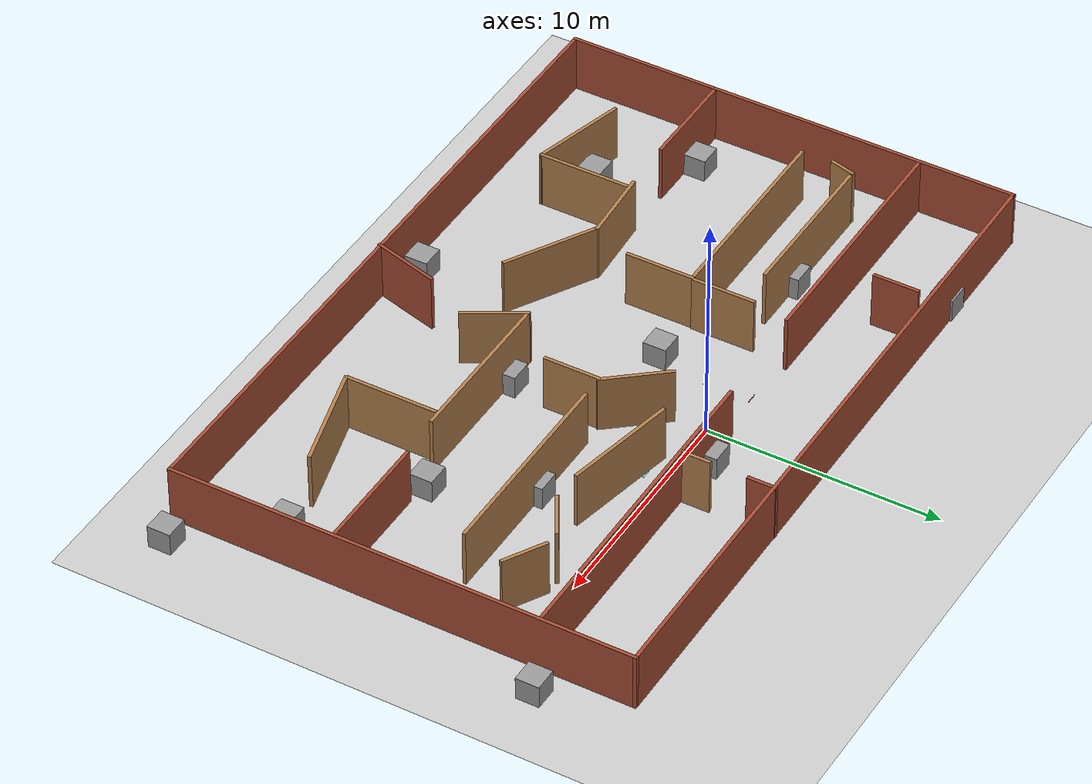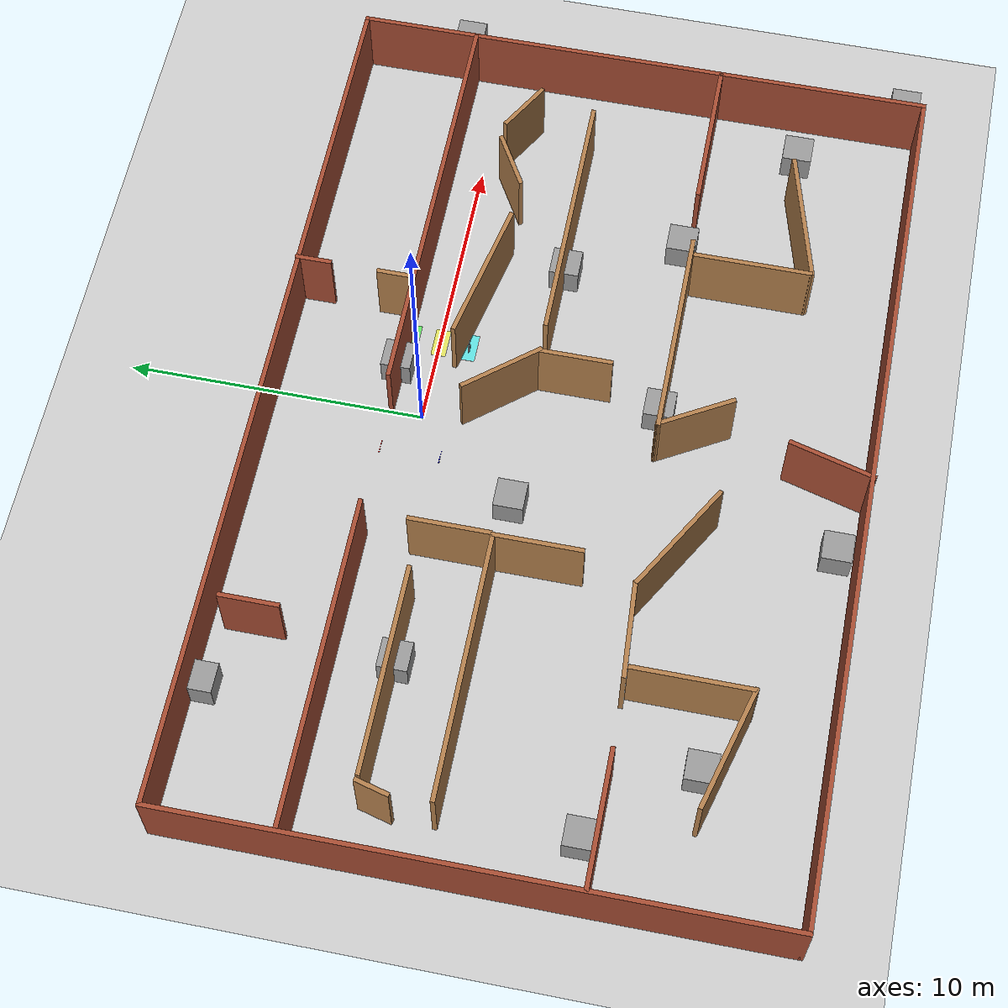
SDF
<?xml version='1.0' encoding='utf-8'?>
<sdf version="1.7">
  <world name="my_world">
    <model name="ground_plane">
      <static>1</static>
      <link name="link">
        <collision name="collision">
          <geometry>
            <plane>
              <normal>0 0 1</normal>
              <size>100 100</size>
            </plane>
          </geometry>
          <surface>
            <contact>
              <collide_bitmask>65535</collide_bitmask>
              <ode />
            </contact>
            <friction>
              <ode>
                <mu>100</mu>
                <mu2>50</mu2>
              </ode>
              <torsional>
                <ode />
              </torsional>
            </friction>
            <bounce />
          </surface>
          <max_contacts>10</max_contacts>
        </collision>
        <visual name="visual">
          <cast_shadows>0</cast_shadows>
          <geometry>
            <plane>
              <normal>0 0 1</normal>
              <size>100 100</size>
            </plane>
          </geometry>
          <material>
            <script>
              <uri>file://media/materials/scripts/gazebo.material</uri>
              <name>Gazebo/Grey</name>
            </script>
          </material>
        </visual>
        <self_collide>0</self_collide>
        <enable_wind>0</enable_wind>
        <kinematic>0</kinematic>
      </link>
    </model>
    <light name="sun" type="directional">
      <cast_shadows>1</cast_shadows>
      <pose>0 0 10 0 -0 0</pose>
      <diffuse>0.8 0.8 0.8 1</diffuse>
      <specular>0.2 0.2 0.2 1</specular>
      <attenuation>
        <range>1000</range>
        <constant>0.9</constant>
        <linear>0.01</linear>
        <quadratic>0.001</quadratic>
      </attenuation>
      <direction>-0.5 0.1 -0.9</direction>
      <spot>
        <inner_angle>0</inner_angle>
        <outer_angle>0</outer_angle>
        <falloff>0</falloff>
      </spot>
    </light>
    <model name="officeroom">
      <pose>-0.693163 -4.92976 0 0 -0 0</pose>
      <link name="Wall_10">
        <collision name="Wall_10_Collision">
          <geometry>
            <box>
              <size>20 0.15 2.5</size>
            </box>
          </geometry>
          <pose>0 0 1.25 0 -0 0</pose>
          <max_contacts>10</max_contacts>
          <surface>
            <contact>
              <ode />
            </contact>
            <bounce />
            <friction>
              <torsional>
                <ode />
              </torsional>
              <ode />
            </friction>
          </surface>
        </collision>
        <visual name="Wall_10_Visual">
          <pose>0 0 1.25 0 -0 0</pose>
          <geometry>
            <box>
              <size>20 0.15 2.5</size>
            </box>
          </geometry>
          <material>
            <script>
              <uri>file://media/materials/scripts/gazebo.material</uri>
              <name>Gazebo/Bricks</name>
            </script>
            <ambient>1 1 1 1</ambient>
          </material>
          <meta>
            <layer>0</layer>
          </meta>
        </visual>
        <pose>14.925 0.014919 0 0 -0 -1.57081</pose>
        <self_collide>0</self_collide>
        <enable_wind>0</enable_wind>
        <kinematic>0</kinematic>
      </link>
      <link name="Wall_107">
        <collision name="Wall_107_Collision">
          <geometry>
            <box>
              <size>3.27854 0.15 2.5</size>
            </box>
          </geometry>
          <pose>0 0 1.25 0 -0 0</pose>
          <max_contacts>10</max_contacts>
          <surface>
            <contact>
              <ode />
            </contact>
            <bounce />
            <friction>
              <torsional>
                <ode />
              </torsional>
              <ode />
            </friction>
          </surface>
        </collision>
        <visual name="Wall_107_Visual">
          <pose>0 0 1.25 0 -0 0</pose>
          <geometry>
            <box>
              <size>3.27854 0.15 2.5</size>
            </box>
          </geometry>
          <material>
            <script>
              <uri>file://media/materials/scripts/gazebo.material</uri>
              <name>Gazebo/Wood</name>
            </script>
            <ambient>1 1 1 1</ambient>
          </material>
          <meta>
            <layer>0</layer>
          </meta>
        </visual>
        <pose>-6.58027 -3.242 0 0 -0 -3.08207</pose>
        <self_collide>0</self_collide>
        <enable_wind>0</enable_wind>
        <kinematic>0</kinematic>
      </link>
      <link name="Wall_109">
        <collision name="Wall_109_Collision">
          <geometry>
            <box>
              <size>4.5 0.15 2.5</size>
            </box>
          </geometry>
          <pose>0 0 1.25 0 -0 0</pose>
          <max_contacts>10</max_contacts>
          <surface>
            <contact>
              <ode />
            </contact>
            <bounce />
            <friction>
              <torsional>
                <ode />
              </torsional>
              <ode />
            </friction>
          </surface>
        </collision>
        <visual name="Wall_109_Visual">
          <pose>0 0 1.25 0 -0 0</pose>
          <geometry>
            <box>
              <size>4.5 0.15 2.5</size>
            </box>
          </geometry>
          <material>
            <script>
              <uri>file://media/materials/scripts/gazebo.material</uri>
              <name>Gazebo/Bricks</name>
            </script>
            <ambient>1 1 1 1</ambient>
          </material>
          <meta>
            <layer>0</layer>
          </meta>
        </visual>
        <pose>-12.6881 -3.41033 0 0 -0 0</pose>
        <self_collide>0</self_collide>
        <enable_wind>0</enable_wind>
        <kinematic>0</kinematic>
      </link>
      <link name="Wall_113">
        <collision name="Wall_113_Collision">
          <geometry>
            <box>
              <size>7.25 0.15 2.5</size>
            </box>
          </geometry>
          <pose>0 0 1.25 0 -0 0</pose>
          <max_contacts>10</max_contacts>
          <surface>
            <contact>
              <ode />
            </contact>
            <bounce />
            <friction>
              <torsional>
                <ode />
              </torsional>
              <ode />
            </friction>
          </surface>
        </collision>
        <visual name="Wall_113_Visual">
          <pose>0 0 1.25 0 -0 0</pose>
          <geometry>
            <box>
              <size>7.25 0.15 2.5</size>
            </box>
          </geometry>
          <material>
            <script>
              <uri>file://media/materials/scripts/gazebo.material</uri>
              <name>Gazebo/Wood</name>
            </script>
            <ambient>1 1 1 1</ambient>
          </material>
          <meta>
            <layer>0</layer>
          </meta>
        </visual>
        <pose>4.22386 -2.91887 0 0 -0 0</pose>
        <self_collide>0</self_collide>
        <enable_wind>0</enable_wind>
        <kinematic>0</kinematic>
      </link>
      <link name="Wall_115">
        <collision name="Wall_115_Collision">
          <geometry>
            <box>
              <size>5.25 0.15 2.5</size>
            </box>
          </geometry>
          <pose>0 0 1.25 0 -0 0</pose>
          <max_contacts>10</max_contacts>
          <surface>
            <contact>
              <ode />
            </contact>
            <bounce />
            <friction>
              <torsional>
                <ode />
              </torsional>
              <ode />
            </friction>
          </surface>
        </collision>
        <visual name="Wall_115_Visual">
          <pose>0 0 1.25 0 -0 0</pose>
          <geometry>
            <box>
              <size>5.25 0.15 2.5</size>
            </box>
          </geometry>
          <material>
            <script>
              <uri>file://media/materials/scripts/gazebo.material</uri>
              <name>Gazebo/Bricks</name>
            </script>
            <ambient>1 1 1 1</ambient>
          </material>
          <meta>
            <layer>0</layer>
          </meta>
        </visual>
        <pose>12.3137 -2.7793 0 0 -0 3.14159</pose>
        <self_collide>0</self_collide>
        <enable_wind>0</enable_wind>
        <kinematic>0</kinematic>
      </link>
      <link name="Wall_118">
        <collision name="Wall_118_Collision">
          <geometry>
            <box>
              <size>2.5 0.15 2.5</size>
            </box>
          </geometry>
          <pose>0 0 1.25 0 -0 0</pose>
          <max_contacts>10</max_contacts>
          <surface>
            <contact>
              <ode />
            </contact>
            <bounce />
            <friction>
              <torsional>
                <ode />
              </torsional>
              <ode />
            </friction>
          </surface>
        </collision>
        <visual name="Wall_118_Visual">
          <pose>0 0 1.25 0 -0 0</pose>
          <geometry>
            <box>
              <size>2.5 0.15 2.5</size>
            </box>
          </geometry>
          <material>
            <script>
              <uri>file://media/materials/scripts/gazebo.material</uri>
              <name>Gazebo/Wood</name>
            </script>
            <ambient>1 1 1 1</ambient>
          </material>
          <meta>
            <layer>0</layer>
          </meta>
        </visual>
        <pose>2.60295 0.147134 0 0 -0 -1.5708</pose>
        <self_collide>0</self_collide>
        <enable_wind>0</enable_wind>
        <kinematic>0</kinematic>
      </link>
      <link name="Wall_12">
        <collision name="Wall_12_Collision">
          <geometry>
            <box>
              <size>30 0.15 2.5</size>
            </box>
          </geometry>
          <pose>0 0 1.25 0 -0 0</pose>
          <max_contacts>10</max_contacts>
          <surface>
            <contact>
              <ode />
            </contact>
            <bounce />
            <friction>
              <torsional>
                <ode />
              </torsional>
              <ode />
            </friction>
          </surface>
        </collision>
        <visual name="Wall_12_Visual">
          <pose>0 0 1.25 0 -0 0</pose>
          <geometry>
            <box>
              <size>30 0.15 2.5</size>
            </box>
          </geometry>
          <material>
            <script>
              <uri>file://media/materials/scripts/gazebo.material</uri>
              <name>Gazebo/Bricks</name>
            </script>
            <ambient>1 1 1 1</ambient>
          </material>
          <meta>
            <layer>0</layer>
          </meta>
        </visual>
        <pose>-0.000162 -9.90993 0 0 -0 3.14159</pose>
        <self_collide>0</self_collide>
        <enable_wind>0</enable_wind>
        <kinematic>0</kinematic>
      </link>
      <link name="Wall_120">
        <collision name="Wall_120_Collision">
          <geometry>
            <box>
              <size>2.75 0.15 2.5</size>
            </box>
          </geometry>
          <pose>0 0 1.25 0 -0 0</pose>
          <max_contacts>10</max_contacts>
          <surface>
            <contact>
              <ode />
            </contact>
            <bounce />
            <friction>
              <torsional>
                <ode />
              </torsional>
              <ode />
            </friction>
          </surface>
        </collision>
        <visual name="Wall_120_Visual">
          <pose>0 0 1.25 0 -0 0</pose>
          <geometry>
            <box>
              <size>2.75 0.15 2.5</size>
            </box>
          </geometry>
          <material>
            <script>
              <uri>file://media/materials/scripts/gazebo.material</uri>
              <name>Gazebo/Wood</name>
            </script>
            <ambient>1 1 1 1</ambient>
          </material>
          <meta>
            <layer>0</layer>
          </meta>
        </visual>
        <pose>1.32386 -4.0447 0 0 -0 -1.0472</pose>
        <self_collide>0</self_collide>
        <enable_wind>0</enable_wind>
        <kinematic>0</kinematic>
      </link>
      <link name="Wall_125">
        <collision name="Wall_125_Collision">
          <geometry>
            <box>
              <size>4 0.15 2.5</size>
            </box>
          </geometry>
          <pose>0 0 1.25 0 -0 0</pose>
          <max_contacts>10</max_contacts>
          <surface>
            <contact>
              <ode />
            </contact>
            <bounce />
            <friction>
              <torsional>
                <ode />
              </torsional>
              <ode />
            </friction>
          </surface>
        </collision>
        <visual name="Wall_125_Visual">
          <pose>0 0 1.25 0 -0 0</pose>
          <geometry>
            <box>
              <size>4 0.15 2.5</size>
            </box>
          </geometry>
          <material>
            <script>
              <uri>file://media/materials/scripts/gazebo.material</uri>
              <name>Gazebo/Wood</name>
            </script>
            <ambient>1 1 1 1</ambient>
          </material>
          <meta>
            <layer>0</layer>
          </meta>
        </visual>
        <pose>-7.82101 -5.406 0 0 -0 -1.5708</pose>
        <self_collide>0</self_collide>
        <enable_wind>0</enable_wind>
        <kinematic>0</kinematic>
      </link>
      <link name="Wall_127">
        <collision name="Wall_127_Collision">
          <geometry>
            <box>
              <size>4 0.15 2.5</size>
            </box>
          </geometry>
          <pose>0 0 1.25 0 -0 0</pose>
          <max_contacts>10</max_contacts>
          <surface>
            <contact>
              <ode />
            </contact>
            <bounce />
            <friction>
              <torsional>
                <ode />
              </torsional>
              <ode />
            </friction>
          </surface>
        </collision>
        <visual name="Wall_127_Visual">
          <pose>0 0 1.25 0 -0 0</pose>
          <geometry>
            <box>
              <size>4 0.15 2.5</size>
            </box>
          </geometry>
          <material>
            <script>
              <uri>file://media/materials/scripts/gazebo.material</uri>
              <name>Gazebo/Wood</name>
            </script>
            <ambient>1 1 1 1</ambient>
          </material>
          <meta>
            <layer>0</layer>
          </meta>
        </visual>
        <pose>7.28181 -5.01384 0 0 -0 -1.5708</pose>
        <self_collide>0</self_collide>
        <enable_wind>0</enable_wind>
        <kinematic>0</kinematic>
      </link>
      <link name="Wall_129">
        <collision name="Wall_129_Collision">
          <geometry>
            <box>
              <size>4.25 0.15 2.5</size>
            </box>
          </geometry>
          <pose>0 0 1.25 0 -0 0</pose>
          <max_contacts>10</max_contacts>
          <surface>
            <contact>
              <ode />
            </contact>
            <bounce />
            <friction>
              <torsional>
                <ode />
              </torsional>
              <ode />
            </friction>
          </surface>
        </collision>
        <visual name="Wall_129_Visual">
          <pose>0 0 1.25 0 -0 0</pose>
          <geometry>
            <box>
              <size>4.25 0.15 2.5</size>
            </box>
          </geometry>
          <material>
            <script>
              <uri>file://media/materials/scripts/gazebo.material</uri>
              <name>Gazebo/Wood</name>
            </script>
            <ambient>1 1 1 1</ambient>
          </material>
          <meta>
            <layer>0</layer>
          </meta>
        </visual>
        <pose>-9.80116 -6.80042 0 0 -0 2.87979</pose>
        <self_collide>0</self_collide>
        <enable_wind>0</enable_wind>
        <kinematic>0</kinematic>
      </link>
      <link name="Wall_132">
        <collision name="Wall_132_Collision">
          <geometry>
            <box>
              <size>4.75 0.15 2.5</size>
            </box>
          </geometry>
          <pose>0 0 1.25 0 -0 0</pose>
          <max_contacts>10</max_contacts>
          <surface>
            <contact>
              <ode />
            </contact>
            <bounce />
            <friction>
              <torsional>
                <ode />
              </torsional>
              <ode />
            </friction>
          </surface>
        </collision>
        <visual name="Wall_132_Visual">
          <pose>0 0 1.25 0 -0 0</pose>
          <geometry>
            <box>
              <size>4.75 0.15 2.5</size>
            </box>
          </geometry>
          <material>
            <script>
              <uri>file://media/materials/scripts/gazebo.material</uri>
              <name>Gazebo/Wood</name>
            </script>
            <ambient>1 1 1 1</ambient>
          </material>
          <meta>
            <layer>0</layer>
          </meta>
        </visual>
        <pose>9.51735 -6.40461 0 0 -0 0.261799</pose>
        <self_collide>0</self_collide>
        <enable_wind>0</enable_wind>
        <kinematic>0</kinematic>
      </link>
      <link name="Wall_134">
        <collision name="Wall_134_Collision">
          <geometry>
            <box>
              <size>3 0.15 2.5</size>
            </box>
          </geometry>
          <pose>0 0 1.25 0 -0 0</pose>
          <max_contacts>10</max_contacts>
          <surface>
            <contact>
              <ode />
            </contact>
            <bounce />
            <friction>
              <torsional>
                <ode />
              </torsional>
              <ode />
            </friction>
          </surface>
        </collision>
        <visual name="Wall_134_Visual">
          <pose>0 0 1.25 0 -0 0</pose>
          <geometry>
            <box>
              <size>3 0.15 2.5</size>
            </box>
          </geometry>
          <material>
            <script>
              <uri>file://media/materials/scripts/gazebo.material</uri>
              <name>Gazebo/Bricks</name>
            </script>
            <ambient>1 1 1 1</ambient>
          </material>
          <meta>
            <layer>0</layer>
          </meta>
        </visual>
        <pose>0.445972 -8.57754 0 0 -0 1.309</pose>
        <self_collide>0</self_collide>
        <enable_wind>0</enable_wind>
        <kinematic>0</kinematic>
      </link>
      <link name="Wall_15">
        <collision name="Wall_15_Collision">
          <geometry>
            <box>
              <size>20 0.15 2.5</size>
            </box>
          </geometry>
          <pose>0 0 1.25 0 -0 0</pose>
          <max_contacts>10</max_contacts>
          <surface>
            <contact>
              <ode />
            </contact>
            <bounce />
            <friction>
              <torsional>
                <ode />
              </torsional>
              <ode />
            </friction>
          </surface>
        </collision>
        <visual name="Wall_15_Visual">
          <pose>0 0 1.25 0 -0 0</pose>
          <geometry>
            <box>
              <size>20 0.15 2.5</size>
            </box>
          </geometry>
          <material>
            <script>
              <uri>file://media/materials/scripts/gazebo.material</uri>
              <name>Gazebo/Bricks</name>
            </script>
            <ambient>1 1 1 1</ambient>
          </material>
          <meta>
            <layer>0</layer>
          </meta>
        </visual>
        <pose>-14.9252 0.015073 0 0 -0 1.5708</pose>
        <self_collide>0</self_collide>
        <enable_wind>0</enable_wind>
        <kinematic>0</kinematic>
      </link>
      <link name="Wall_2">
        <collision name="Wall_2_Collision">
          <geometry>
            <box>
              <size>30 0.15 2.5</size>
            </box>
          </geometry>
          <pose>0 0 1.25 0 -0 0</pose>
          <max_contacts>10</max_contacts>
          <surface>
            <contact>
              <ode />
            </contact>
            <bounce />
            <friction>
              <torsional>
                <ode />
              </torsional>
              <ode />
            </friction>
          </surface>
        </collision>
        <visual name="Wall_2_Visual">
          <pose>0 0 1.25 0 -0 0</pose>
          <geometry>
            <box>
              <size>30 0.15 2.5</size>
            </box>
          </geometry>
          <material>
            <script>
              <uri>file://media/materials/scripts/gazebo.material</uri>
              <name>Gazebo/Bricks</name>
            </script>
            <ambient>1 1 1 1</ambient>
          </material>
          <meta>
            <layer>0</layer>
          </meta>
        </visual>
        <pose>0.000163 9.93976 0 0 -0 0</pose>
        <self_collide>0</self_collide>
        <enable_wind>0</enable_wind>
        <kinematic>0</kinematic>
      </link>
      <link name="Wall_29">
        <collision name="Wall_29_Collision">
          <geometry>
            <box>
              <size>1.25 0.15 2.5</size>
            </box>
          </geometry>
          <pose>0 0 1.25 0 -0 0</pose>
          <max_contacts>10</max_contacts>
          <surface>
            <contact>
              <ode />
            </contact>
            <bounce />
            <friction>
              <torsional>
                <ode />
              </torsional>
              <ode />
            </friction>
          </surface>
        </collision>
        <visual name="Wall_29_Visual">
          <pose>0 0 1.25 0 -0 0</pose>
          <geometry>
            <box>
              <size>1.25 0.15 2.5</size>
            </box>
          </geometry>
          <material>
            <script>
              <uri>file://media/materials/scripts/gazebo.material</uri>
              <name>Gazebo/Bricks</name>
            </script>
            <ambient>1 1 1 1</ambient>
          </material>
          <meta>
            <layer>0</layer>
          </meta>
        </visual>
        <pose>4.61028 9.42084 0 0 -0 -1.5708</pose>
        <self_collide>0</self_collide>
        <enable_wind>0</enable_wind>
        <kinematic>0</kinematic>
      </link>
      <link name="Wall_31">
        <collision name="Wall_31_Collision">
          <geometry>
            <box>
              <size>1.25 0.15 2.5</size>
            </box>
          </geometry>
          <pose>0 0 1.25 0 -0 0</pose>
          <max_contacts>10</max_contacts>
          <surface>
            <contact>
              <ode />
            </contact>
            <bounce />
            <friction>
              <torsional>
                <ode />
              </torsional>
              <ode />
            </friction>
          </surface>
        </collision>
        <visual name="Wall_31_Visual">
          <pose>0 0 1.25 0 -0 0</pose>
          <geometry>
            <box>
              <size>1.25 0.15 2.5</size>
            </box>
          </geometry>
          <material>
            <script>
              <uri>file://media/materials/scripts/gazebo.material</uri>
              <name>Gazebo/Wood</name>
            </script>
            <ambient>1 1 1 1</ambient>
          </material>
          <meta>
            <layer>0</layer>
          </meta>
        </visual>
        <pose>4.59016 6.61881 0 0 -0 1.5708</pose>
        <self_collide>0</self_collide>
        <enable_wind>0</enable_wind>
        <kinematic>0</kinematic>
      </link>
      <link name="Wall_34">
        <collision name="Wall_34_Collision">
          <geometry>
            <box>
              <size>2 0.15 2.5</size>
            </box>
          </geometry>
          <pose>0 0 1.25 0 -0 0</pose>
          <max_contacts>10</max_contacts>
          <surface>
            <contact>
              <ode />
            </contact>
            <bounce />
            <friction>
              <torsional>
                <ode />
              </torsional>
              <ode />
            </friction>
          </surface>
        </collision>
        <visual name="Wall_34_Visual">
          <pose>0 0 1.25 0 -0 0</pose>
          <geometry>
            <box>
              <size>2 0.15 2.5</size>
            </box>
          </geometry>
          <material>
            <script>
              <uri>file://media/materials/scripts/gazebo.material</uri>
              <name>Gazebo/Bricks</name>
            </script>
            <ambient>1 1 1 1</ambient>
          </material>
          <meta>
            <layer>0</layer>
          </meta>
        </visual>
        <pose>-7.92097 8.43964 0 0 -0 -1.5708</pose>
        <self_collide>0</self_collide>
        <enable_wind>0</enable_wind>
        <kinematic>0</kinematic>
      </link>
      <link name="Wall_38">
        <collision name="Wall_38_Collision">
          <geometry>
            <box>
              <size>11 0.15 2.5</size>
            </box>
          </geometry>
          <pose>0 0 1.25 0 -0 0</pose>
          <max_contacts>10</max_contacts>
          <surface>
            <contact>
              <ode />
            </contact>
            <bounce />
            <friction>
              <torsional>
                <ode />
              </torsional>
              <ode />
            </friction>
          </surface>
        </collision>
        <visual name="Wall_38_Visual">
          <pose>0 0 1.25 0 -0 0</pose>
          <geometry>
            <box>
              <size>11 0.15 2.5</size>
            </box>
          </geometry>
          <material>
            <script>
              <uri>file://media/materials/scripts/gazebo.material</uri>
              <name>Gazebo/Bricks</name>
            </script>
            <ambient>1 1 1 1</ambient>
          </material>
          <meta>
            <layer>0</layer>
          </meta>
        </visual>
        <pose>-9.35541 5.8262 0 0 -0 0</pose>
        <self_collide>0</self_collide>
        <enable_wind>0</enable_wind>
        <kinematic>0</kinematic>
      </link>
      <link name="Wall_40">
        <collision name="Wall_40_Collision">
          <geometry>
            <box>
              <size>14.25 0.15 2.5</size>
            </box>
          </geometry>
          <pose>0 0 1.25 0 -0 0</pose>
          <max_contacts>10</max_contacts>
          <surface>
            <contact>
              <ode />
            </contact>
            <bounce />
            <friction>
              <torsional>
                <ode />
              </torsional>
              <ode />
            </friction>
          </surface>
        </collision>
        <visual name="Wall_40_Visual">
          <pose>0 0 1.25 0 -0 0</pose>
          <geometry>
            <box>
              <size>14.25 0.15 2.5</size>
            </box>
          </geometry>
          <material>
            <script>
              <uri>file://media/materials/scripts/gazebo.material</uri>
              <name>Gazebo/Bricks</name>
            </script>
            <ambient>1 1 1 1</ambient>
          </material>
          <meta>
            <layer>0</layer>
          </meta>
        </visual>
        <pose>7.83962 5.98375 0 0 -0 3.14159</pose>
        <self_collide>0</self_collide>
        <enable_wind>0</enable_wind>
        <kinematic>0</kinematic>
      </link>
      <link name="Wall_46">
        <collision name="Wall_46_Collision">
          <geometry>
            <box>
              <size>7.0 0.15 2.5</size>
            </box>
          </geometry>
          <pose>0 0 1.25 0 -0 0</pose>
          <max_contacts>10</max_contacts>
          <surface>
            <contact>
              <ode />
            </contact>
            <bounce />
            <friction>
              <torsional>
                <ode />
              </torsional>
              <ode />
            </friction>
          </surface>
        </collision>
        <visual name="Wall_46_Visual">
          <pose>0 0 1.25 0 -0 0</pose>
          <geometry>
            <box>
              <size>7.0 0.15 2.5</size>
            </box>
          </geometry>
          <material>
            <script>
              <uri>file://media/materials/scripts/gazebo.material</uri>
              <name>Gazebo/Wood</name>
            </script>
            <ambient>1 1 1 1</ambient>
          </material>
          <meta>
            <layer>0</layer>
          </meta>
        </visual>
        <pose>-9.30884 3.8355 0 0 -0 -0.004163</pose>
        <self_collide>0</self_collide>
        <enable_wind>0</enable_wind>
        <kinematic>0</kinematic>
      </link>
      <link name="Wall_49">
        <collision name="Wall_49_Collision">
          <geometry>
            <box>
              <size>1.17019 0.15 2.5</size>
            </box>
          </geometry>
          <pose>0 0 1.25 0 -0 0</pose>
          <max_contacts>10</max_contacts>
          <surface>
            <contact>
              <ode />
            </contact>
            <bounce />
            <friction>
              <torsional>
                <ode />
              </torsional>
              <ode />
            </friction>
          </surface>
        </collision>
        <visual name="Wall_49_Visual">
          <pose>0 0 1.25 0 -0 0</pose>
          <geometry>
            <box>
              <size>1.17019 0.15 2.5</size>
            </box>
          </geometry>
          <material>
            <script>
              <uri>file://media/materials/scripts/gazebo.material</uri>
              <name>Gazebo/Wood</name>
            </script>
            <ambient>1 1 1 1</ambient>
          </material>
          <meta>
            <layer>0</layer>
          </meta>
        </visual>
        <pose>-13.076 3.35727 0 0 -0 -1.82702</pose>
        <self_collide>0</self_collide>
        <enable_wind>0</enable_wind>
        <kinematic>0</kinematic>
      </link>
      <link name="Wall_57">
        <collision name="Wall_57_Collision">
          <geometry>
            <box>
              <size>2.75 0.15 2.5</size>
            </box>
          </geometry>
          <pose>0 0 1.25 0 -0 0</pose>
          <max_contacts>10</max_contacts>
          <surface>
            <contact>
              <ode />
            </contact>
            <bounce />
            <friction>
              <torsional>
                <ode />
              </torsional>
              <ode />
            </friction>
          </surface>
        </collision>
        <visual name="Wall_57_Visual">
          <pose>0 0 1.25 0 -0 0</pose>
          <geometry>
            <box>
              <size>2.75 0.15 2.5</size>
            </box>
          </geometry>
          <material>
            <script>
              <uri>file://media/materials/scripts/gazebo.material</uri>
              <name>Gazebo/Wood</name>
            </script>
            <ambient>1 1 1 1</ambient>
          </material>
          <meta>
            <layer>0</layer>
          </meta>
        </visual>
        <pose>-4.21161 2.89682 0 0 -0 1.5708</pose>
        <self_collide>0</self_collide>
        <enable_wind>0</enable_wind>
        <kinematic>0</kinematic>
      </link>
      <link name="Wall_59">
        <collision name="Wall_59_Collision">
          <geometry>
            <box>
              <size>5.0 0.15 2.5</size>
            </box>
          </geometry>
          <pose>0 0 1.25 0 -0 0</pose>
          <max_contacts>10</max_contacts>
          <surface>
            <contact>
              <ode />
            </contact>
            <bounce />
            <friction>
              <torsional>
                <ode />
              </torsional>
              <ode />
            </friction>
          </surface>
        </collision>
        <visual name="Wall_59_Visual">
          <pose>0 0 1.25 0 -0 0</pose>
          <geometry>
            <box>
              <size>5.0 0.15 2.5</size>
            </box>
          </geometry>
          <material>
            <script>
              <uri>file://media/materials/scripts/gazebo.material</uri>
              <name>Gazebo/Wood</name>
            </script>
            <ambient>1 1 1 1</ambient>
          </material>
          <meta>
            <layer>0</layer>
          </meta>
        </visual>
        <pose>5.28704 3.77735 0 0 -0 -0.202428</pose>
        <self_collide>0</self_collide>
        <enable_wind>0</enable_wind>
        <kinematic>0</kinematic>
      </link>
      <link name="Wall_60">
        <collision name="Wall_60_Collision">
          <geometry>
            <box>
              <size>2.1 0.15 2.5</size>
            </box>
          </geometry>
          <pose>0 0 1.25 0 -0 0</pose>
          <max_contacts>10</max_contacts>
          <surface>
            <contact>
              <ode />
            </contact>
            <bounce />
            <friction>
              <torsional>
                <ode />
              </torsional>
              <ode />
            </friction>
          </surface>
        </collision>
        <visual name="Wall_60_Visual">
          <pose>0 0 1.25 0 -0 0</pose>
          <geometry>
            <box>
              <size>2.1 0.15 2.5</size>
            </box>
          </geometry>
          <material>
            <script>
              <uri>file://media/materials/scripts/gazebo.material</uri>
              <name>Gazebo/Wood</name>
            </script>
            <ambient>1 1 1 1</ambient>
          </material>
          <meta>
            <layer>0</layer>
          </meta>
        </visual>
        <pose>9.88652 3.73459 0 0 -0 0.527727</pose>
        <self_collide>0</self_collide>
        <enable_wind>0</enable_wind>
        <kinematic>0</kinematic>
      </link>
      <link name="Wall_61">
        <collision name="Wall_61_Collision">
          <geometry>
            <box>
              <size>2.0 0.15 2.5</size>
            </box>
          </geometry>
          <pose>0 0 1.25 0 -0 0</pose>
          <max_contacts>10</max_contacts>
          <surface>
            <contact>
              <ode />
            </contact>
            <bounce />
            <friction>
              <torsional>
                <ode />
              </torsional>
              <ode />
            </friction>
          </surface>
        </collision>
        <visual name="Wall_61_Visual">
          <pose>0 0 1.25 0 -0 0</pose>
          <geometry>
            <box>
              <size>2.0 0.15 2.5</size>
            </box>
          </geometry>
          <material>
            <script>
              <uri>file://media/materials/scripts/gazebo.material</uri>
              <name>Gazebo/Wood</name>
            </script>
            <ambient>1 1 1 1</ambient>
          </material>
          <meta>
            <layer>0</layer>
          </meta>
        </visual>
        <pose>12.2003 3.7238 0 0 -0 -0.523599</pose>
        <self_collide>0</self_collide>
        <enable_wind>0</enable_wind>
        <kinematic>0</kinematic>
      </link>
      <link name="Wall_66">
        <collision name="Wall_66_Collision">
          <geometry>
            <box>
              <size>3.01901 0.15 2.5</size>
            </box>
          </geometry>
          <pose>0 0 1.25 0 -0 0</pose>
          <max_contacts>10</max_contacts>
          <surface>
            <contact>
              <ode />
            </contact>
            <bounce />
            <friction>
              <torsional>
                <ode />
              </torsional>
              <ode />
            </friction>
          </surface>
        </collision>
        <visual name="Wall_66_Visual">
          <pose>0 0 1.25 0 -0 0</pose>
          <geometry>
            <box>
              <size>3.01901 0.15 2.5</size>
            </box>
          </geometry>
          <material>
            <script>
              <uri>file://media/materials/scripts/gazebo.material</uri>
              <name>Gazebo/Wood</name>
            </script>
            <ambient>1 1 1 1</ambient>
          </material>
          <meta>
            <layer>0</layer>
          </meta>
        </visual>
        <pose>1.74226 2.43334 0 0 -0 2.25548</pose>
        <self_collide>0</self_collide>
        <enable_wind>0</enable_wind>
        <kinematic>0</kinematic>
      </link>
      <link name="Wall_68">
        <collision name="Wall_68_Collision">
          <geometry>
            <box>
              <size>9 0.15 2.5</size>
            </box>
          </geometry>
          <pose>0 0 1.25 0 -0 0</pose>
          <max_contacts>10</max_contacts>
          <surface>
            <contact>
              <ode />
            </contact>
            <bounce />
            <friction>
              <torsional>
                <ode />
              </torsional>
              <ode />
            </friction>
          </surface>
        </collision>
        <visual name="Wall_68_Visual">
          <pose>0 0 1.25 0 -0 0</pose>
          <geometry>
            <box>
              <size>9 0.15 2.5</size>
            </box>
          </geometry>
          <material>
            <script>
              <uri>file://media/materials/scripts/gazebo.material</uri>
              <name>Gazebo/Wood</name>
            </script>
            <ambient>1 1 1 1</ambient>
          </material>
          <meta>
            <layer>0</layer>
          </meta>
        </visual>
        <pose>-8.68528 1.49923 0 0 -0 3.14159</pose>
        <self_collide>0</self_collide>
        <enable_wind>0</enable_wind>
        <kinematic>0</kinematic>
      </link>
      <link name="Wall_72">
        <collision name="Wall_72_Collision">
          <geometry>
            <box>
              <size>8.9356 0.15 2.5</size>
            </box>
          </geometry>
          <pose>0 0 1.25 0 -0 0</pose>
          <max_contacts>10</max_contacts>
          <surface>
            <contact>
              <ode />
            </contact>
            <bounce />
            <friction>
              <torsional>
                <ode />
              </torsional>
              <ode />
            </friction>
          </surface>
        </collision>
        <visual name="Wall_72_Visual">
          <pose>0 0 1.25 0 -0 0</pose>
          <geometry>
            <box>
              <size>8.9356 0.15 2.5</size>
            </box>
          </geometry>
          <material>
            <script>
              <uri>file://media/materials/scripts/gazebo.material</uri>
              <name>Gazebo/Wood</name>
            </script>
            <ambient>1 1 1 1</ambient>
          </material>
          <meta>
            <layer>0</layer>
          </meta>
        </visual>
        <pose>8.04226 1.32213 0 0 -0 3.14159</pose>
        <self_collide>0</self_collide>
        <enable_wind>0</enable_wind>
        <kinematic>0</kinematic>
      </link>
      <link name="Wall_75">
        <collision name="Wall_75_Collision">
          <geometry>
            <box>
              <size>3 0.15 2.5</size>
            </box>
          </geometry>
          <pose>0 0 1.25 0 -0 0</pose>
          <max_contacts>10</max_contacts>
          <surface>
            <contact>
              <ode />
            </contact>
            <bounce />
            <friction>
              <torsional>
                <ode />
              </torsional>
              <ode />
            </friction>
          </surface>
        </collision>
        <visual name="Wall_75_Visual">
          <pose>0 0 1.25 0 -0 0</pose>
          <geometry>
            <box>
              <size>3 0.15 2.5</size>
            </box>
          </geometry>
          <material>
            <script>
              <uri>file://media/materials/scripts/gazebo.material</uri>
              <name>Gazebo/Wood</name>
            </script>
            <ambient>1 1 1 1</ambient>
          </material>
          <meta>
            <layer>0</layer>
          </meta>
        </visual>
        <pose>-4.26028 0.074229 0 0 -0 -1.5708</pose>
        <self_collide>0</self_collide>
        <enable_wind>0</enable_wind>
        <kinematic>0</kinematic>
      </link>
      <link name="Wall_81">
        <collision name="Wall_81_Collision">
          <geometry>
            <box>
              <size>4.25 0.15 2.5</size>
            </box>
          </geometry>
          <pose>0 0 1.25 0 -0 0</pose>
          <max_contacts>10</max_contacts>
          <surface>
            <contact>
              <ode />
            </contact>
            <bounce />
            <friction>
              <torsional>
                <ode />
              </torsional>
              <ode />
            </friction>
          </surface>
        </collision>
        <visual name="Wall_81_Visual">
          <pose>0 0 1.25 0 -0 0</pose>
          <geometry>
            <box>
              <size>4.25 0.15 2.5</size>
            </box>
          </geometry>
          <material>
            <script>
              <uri>file://media/materials/scripts/gazebo.material</uri>
              <name>Gazebo/Wood</name>
            </script>
            <ambient>1 1 1 1</ambient>
          </material>
          <meta>
            <layer>0</layer>
          </meta>
        </visual>
        <pose>-3.1969 -4.22048 0 0 -0 -0.523599</pose>
        <self_collide>0</self_collide>
        <enable_wind>0</enable_wind>
        <kinematic>0</kinematic>
      </link>
      <static>1</static>
    </model>
    <gravity>0 0 -9.8</gravity>
    <magnetic_field>6e-06 2.3e-05 -4.2e-05</magnetic_field>
    <atmosphere type="adiabatic" />
    <scene>
      <ambient>0.4 0.4 0.4 1</ambient>
      <background>0.7 0.7 0.7 1</background>
      <shadows>1</shadows>
    </scene>
    <audio>
      <device>default</device>
    </audio>
    <wind />
    <spherical_coordinates>
      <surface_model>EARTH_WGS84</surface_model>
      <latitude_deg>0</latitude_deg>
      <longitude_deg>0</longitude_deg>
      <elevation>0</elevation>
      <heading_deg>0</heading_deg>
    </spherical_coordinates>
    <model name="red_cube_1">
      <pose>-1.5 1 0.75 0 -0 0</pose>
      <link name="link">
        <inertial>
          <mass>0.1</mass>
        </inertial>
        <gravity>0</gravity>
        <collision name="collision">
          <laser_retro>130</laser_retro>
          <geometry>
            <box>
              <size>0.03 0.03 0.03</size>
            </box>
          </geometry>
          <surface>
            <contact>
              <collide_bitmask>0</collide_bitmask>
            </contact>
          </surface>
        </collision>
        <visual name="visual">
          <geometry>
            <box>
              <size>0.03 0.03 0.03</size>
            </box>
          </geometry>
          <material>
            <ambient>1 0 0 1</ambient>
            <diffuse>1 0 0 1</diffuse>
          </material>
        </visual>
      </link>
    </model>
    <model name="red_cube_2">
      <pose>-1.6 1 0.75 0 -0 0</pose>
      <link name="link">
        <inertial>
          <mass>0.1</mass>
        </inertial>
        <gravity>0</gravity>
        <collision name="collision">
          <laser_retro>130</laser_retro>
          <geometry>
            <box>
              <size>0.03 0.03 0.03</size>
            </box>
          </geometry>
          <surface>
            <contact>
              <collide_bitmask>0</collide_bitmask>
            </contact>
          </surface>
        </collision>
        <visual name="visual">
          <geometry>
            <box>
              <size>0.03 0.03 0.03</size>
            </box>
          </geometry>
          <material>
            <ambient>1 0 0 1</ambient>
            <diffuse>1 0 0 1</diffuse>
          </material>
        </visual>
      </link>
    </model>
    <model name="red_cube_3">
      <pose>-1.7 1 0.75 0 -0 0</pose>
      <link name="link">
        <inertial>
          <mass>0.1</mass>
        </inertial>
        <gravity>0</gravity>
        <collision name="collision">
          <laser_retro>130</laser_retro>
          <geometry>
            <box>
              <size>0.03 0.03 0.03</size>
            </box>
          </geometry>
          <surface>
            <contact>
              <collide_bitmask>0</collide_bitmask>
            </contact>
          </surface>
        </collision>
        <visual name="visual">
          <geometry>
            <box>
              <size>0.03 0.03 0.03</size>
            </box>
          </geometry>
          <material>
            <ambient>1 0 0 1</ambient>
            <diffuse>1 0 0 1</diffuse>
          </material>
        </visual>
      </link>
    </model>
    <model name="red_cube_4">
      <pose>-1.8 1 0.75 0 -0 0</pose>
      <link name="link">
        <inertial>
          <mass>0.1</mass>
        </inertial>
        <gravity>0</gravity>
        <collision name="collision">
          <laser_retro>130</laser_retro>
          <geometry>
            <box>
              <size>0.03 0.03 0.03</size>
            </box>
          </geometry>
          <surface>
            <contact>
              <collide_bitmask>0</collide_bitmask>
            </contact>
          </surface>
        </collision>
        <visual name="visual">
          <geometry>
            <box>
              <size>0.03 0.03 0.03</size>
            </box>
          </geometry>
          <material>
            <ambient>1 0 0 1</ambient>
            <diffuse>1 0 0 1</diffuse>
          </material>
        </visual>
      </link>
    </model>
    <model name="red_cube_5">
      <pose>-1.9 1 0.75 0 -0 0</pose>
      <link name="link">
        <inertial>
          <mass>0.1</mass>
        </inertial>
        <gravity>0</gravity>
        <collision name="collision">
          <laser_retro>130</laser_retro>
          <geometry>
            <box>
              <size>0.03 0.03 0.03</size>
            </box>
          </geometry>
          <surface>
            <contact>
              <collide_bitmask>0</collide_bitmask>
            </contact>
          </surface>
        </collision>
        <visual name="visual">
          <geometry>
            <box>
              <size>0.03 0.03 0.03</size>
            </box>
          </geometry>
          <material>
            <ambient>1 0 0 1</ambient>
            <diffuse>1 0 0 1</diffuse>
          </material>
        </visual>
      </link>
    </model>
    <model name="blue_cube_1">
      <pose>-1.5 -1 0.75 0 -0 0</pose>
      <link name="link">
        <inertial>
          <mass>0.1</mass>
        </inertial>
        <gravity>0</gravity>
        <collision name="collision">
          <laser_retro>130</laser_retro>
          <geometry>
            <box>
              <size>0.03 0.03 0.03</size>
            </box>
          </geometry>
          <surface>
            <contact>
              <collide_bitmask>0</collide_bitmask>
            </contact>
          </surface>
        </collision>
        <visual name="visual">
          <geometry>
            <box>
              <size>0.03 0.03 0.03</size>
            </box>
          </geometry>
          <material>
            <ambient>0 0 1 1</ambient>
            <diffuse>0 0 1 1</diffuse>
          </material>
        </visual>
      </link>
    </model>
    <model name="blue_cube_2">
      <pose>-1.6 -1 0.75 0 -0 0</pose>
      <link name="link">
        <inertial>
          <mass>0.1</mass>
        </inertial>
        <gravity>0</gravity>
        <collision name="collision">
          <laser_retro>130</laser_retro>
          <geometry>
            <box>
              <size>0.03 0.03 0.03</size>
            </box>
          </geometry>
          <surface>
            <contact>
              <collide_bitmask>0</collide_bitmask>
            </contact>
          </surface>
        </collision>
        <visual name="visual">
          <geometry>
            <box>
              <size>0.03 0.03 0.03</size>
            </box>
          </geometry>
          <material>
            <ambient>0 0 1 1</ambient>
            <diffuse>0 0 1 1</diffuse>
          </material>
        </visual>
      </link>
    </model>
    <model name="blue_cube_3">
      <pose>-1.7 -1 0.75 0 -0 0</pose>
      <link name="link">
        <inertial>
          <mass>0.1</mass>
        </inertial>
        <gravity>0</gravity>
        <collision name="collision">
          <laser_retro>130</laser_retro>
          <geometry>
            <box>
              <size>0.03 0.03 0.03</size>
            </box>
          </geometry>
          <surface>
            <contact>
              <collide_bitmask>0</collide_bitmask>
            </contact>
          </surface>
        </collision>
        <visual name="visual">
          <geometry>
            <box>
              <size>0.03 0.03 0.03</size>
            </box>
          </geometry>
          <material>
            <ambient>0 0 1 1</ambient>
            <diffuse>0 0 1 1</diffuse>
          </material>
        </visual>
      </link>
    </model>
    <model name="blue_cube_4">
      <pose>-1.8 -1 0.75 0 -0 0</pose>
      <link name="link">
        <inertial>
          <mass>0.1</mass>
        </inertial>
        <gravity>0</gravity>
        <collision name="collision">
          <laser_retro>130</laser_retro>
          <geometry>
            <box>
              <size>0.03 0.03 0.03</size>
            </box>
          </geometry>
          <surface>
            <contact>
              <collide_bitmask>0</collide_bitmask>
            </contact>
          </surface>
        </collision>
        <visual name="visual">
          <geometry>
            <box>
              <size>0.03 0.03 0.03</size>
            </box>
          </geometry>
          <material>
            <ambient>0 0 1 1</ambient>
            <diffuse>0 0 1 1</diffuse>
          </material>
        </visual>
      </link>
    </model>
    <model name="blue_cube_5">
      <pose>-1.9 -1 0.75 0 -0 0</pose>
      <link name="link">
        <inertial>
          <mass>0.1</mass>
        </inertial>
        <gravity>0</gravity>
        <collision name="collision">
          <laser_retro>130</laser_retro>
          <geometry>
            <box>
              <size>0.03 0.03 0.03</size>
            </box>
          </geometry>
          <surface>
            <contact>
              <collide_bitmask>0</collide_bitmask>
            </contact>
          </surface>
        </collision>
        <visual name="visual">
          <geometry>
            <box>
              <size>0.03 0.03 0.03</size>
            </box>
          </geometry>
          <material>
            <ambient>0 0 1 1</ambient>
            <diffuse>0 0 1 1</diffuse>
          </material>
        </visual>
      </link>
    </model>
    <model name="zone_a">
      <static>1</static>
      <pose>3 1 0.01 0 -0 0</pose>
      <link name="base">
        <visual name="visual">
          <geometry>
            <box>
              <size>1 0.5 0.02</size>
            </box>
          </geometry>
          <material>
            <ambient>0 1 0 0.5</ambient>
            <diffuse>0 1 0 0.5</diffuse>
          </material>
        </visual>
        <self_collide>0</self_collide>
        <enable_wind>0</enable_wind>
        <kinematic>0</kinematic>
      </link>
      <link name="letter_A_1">
        <pose>-0.1 0 0.22 0 0.4 0</pose>
        <visual name="v">
          <geometry>
            <box>
              <size>0.04 0.04 0.4</size>
            </box>
          </geometry>
          <material>
            <ambient>0 0 0 1</ambient>
            <diffuse>0 0 0 1</diffuse>
          </material>
        </visual>
        <self_collide>0</self_collide>
        <enable_wind>0</enable_wind>
        <kinematic>0</kinematic>
      </link>
      <link name="letter_A_2">
        <pose>0.1 0 0.22 0 -0.4 0</pose>
        <visual name="v">
          <geometry>
            <box>
              <size>0.04 0.04 0.4</size>
            </box>
          </geometry>
          <material>
            <ambient>0 0 0 1</ambient>
            <diffuse>0 0 0 1</diffuse>
          </material>
        </visual>
        <self_collide>0</self_collide>
        <enable_wind>0</enable_wind>
        <kinematic>0</kinematic>
      </link>
      <link name="letter_A_3">
        <pose>0 0 0.25 0 -0 0</pose>
        <visual name="v">
          <geometry>
            <box>
              <size>0.15 0.04 0.04</size>
            </box>
          </geometry>
          <material>
            <ambient>0 0 0 1</ambient>
            <diffuse>0 0 0 1</diffuse>
          </material>
        </visual>
        <self_collide>0</self_collide>
        <enable_wind>0</enable_wind>
        <kinematic>0</kinematic>
      </link>
    </model>
    <model name="zone_b">
      <static>1</static>
      <pose>3 0 0.01 0 -0 0</pose>
      <link name="base">
        <visual name="visual">
          <geometry>
            <box>
              <size>1 0.5 0.02</size>
            </box>
          </geometry>
          <material>
            <ambient>1 1 0 0.5</ambient>
            <diffuse>1 1 0 0.5</diffuse>
          </material>
        </visual>
        <self_collide>0</self_collide>
        <enable_wind>0</enable_wind>
        <kinematic>0</kinematic>
      </link>
      <link name="letter_B_vertical_stroke">
        <pose>-0.1 0 0.2 0 -0 0</pose>
        <visual name="v">
          <geometry>
            <box>
              <size>0.04 0.04 0.4</size>
            </box>
          </geometry>
          <material>
            <ambient>0 0 0 1</ambient>
            <diffuse>0 0 0 1</diffuse>
          </material>
        </visual>
        <self_collide>0</self_collide>
        <enable_wind>0</enable_wind>
        <kinematic>0</kinematic>
      </link>
      <link name="letter_B_top_horizontal">
        <pose>0.05 0 0.38 0 -0 0</pose>
        <visual name="v">
          <geometry>
            <box>
              <size>0.25 0.04 0.04</size>
            </box>
          </geometry>
          <material>
            <ambient>0 0 0 1</ambient>
            <diffuse>0 0 0 1</diffuse>
          </material>
        </visual>
        <self_collide>0</self_collide>
        <enable_wind>0</enable_wind>
        <kinematic>0</kinematic>
      </link>
      <link name="letter_B_middle_horizontal">
        <pose>0.05 0 0.2 0 -0 0</pose>
        <visual name="v">
          <geometry>
            <box>
              <size>0.25 0.04 0.04</size>
            </box>
          </geometry>
          <material>
            <ambient>0 0 0 1</ambient>
            <diffuse>0 0 0 1</diffuse>
          </material>
        </visual>
        <self_collide>0</self_collide>
        <enable_wind>0</enable_wind>
        <kinematic>0</kinematic>
      </link>
      <link name="letter_B_bottom_horizontal">
        <pose>0.05 0 0.02 0 -0 0</pose>
        <visual name="v">
          <geometry>
            <box>
              <size>0.25 0.04 0.04</size>
            </box>
          </geometry>
          <material>
            <ambient>0 0 0 1</ambient>
            <diffuse>0 0 0 1</diffuse>
          </material>
        </visual>
        <self_collide>0</self_collide>
        <enable_wind>0</enable_wind>
        <kinematic>0</kinematic>
      </link>
      <link name="letter_B_top_vertical_stroke">
        <pose>0.15 0 0.29 0 -0 0</pose>
        <visual name="v">
          <geometry>
            <box>
              <size>0.04 0.04 0.2</size>
            </box>
          </geometry>
          <material>
            <ambient>0 0 0 1</ambient>
            <diffuse>0 0 0 1</diffuse>
          </material>
        </visual>
        <self_collide>0</self_collide>
        <enable_wind>0</enable_wind>
        <kinematic>0</kinematic>
      </link>
      <link name="letter_B_bottom_vertical_stroke">
        <pose>0.15 0 0.11 0 -0 0</pose>
        <visual name="v">
          <geometry>
            <box>
              <size>0.04 0.04 0.2</size>
            </box>
          </geometry>
          <material>
            <ambient>0 0 0 1</ambient>
            <diffuse>0 0 0 1</diffuse>
          </material>
        </visual>
        <self_collide>0</self_collide>
        <enable_wind>0</enable_wind>
        <kinematic>0</kinematic>
      </link>
    </model>
    <model name="zone_c">
      <static>1</static>
      <pose>3 -1 0.01 0 -0 0</pose>
      <link name="base">
        <visual name="visual">
          <geometry>
            <box>
              <size>1 0.5 0.02</size>
            </box>
          </geometry>
          <material>
            <ambient>0 1 1 0.5</ambient>
            <diffuse>0 1 1 0.5</diffuse>
          </material>
        </visual>
        <self_collide>0</self_collide>
        <enable_wind>0</enable_wind>
        <kinematic>0</kinematic>
      </link>
      <link name="letter_C_1">
        <pose>-0.05 0 0.38 0 -0 0</pose>
        <visual name="v">
          <geometry>
            <box>
              <size>0.3 0.04 0.04</size>
            </box>
          </geometry>
          <material>
            <ambient>0 0 0 1</ambient>
            <diffuse>0 0 0 1</diffuse>
          </material>
        </visual>
        <self_collide>0</self_collide>
        <enable_wind>0</enable_wind>
        <kinematic>0</kinematic>
      </link>
      <link name="letter_C_2">
        <pose>-0.05 0 0.02 0 -0 0</pose>
        <visual name="v">
          <geometry>
            <box>
              <size>0.3 0.04 0.04</size>
            </box>
          </geometry>
          <material>
            <ambient>0 0 0 1</ambient>
            <diffuse>0 0 0 1</diffuse>
          </material>
        </visual>
        <self_collide>0</self_collide>
        <enable_wind>0</enable_wind>
        <kinematic>0</kinematic>
      </link>
      <link name="letter_C_3">
        <pose>-0.18 0 0.2 0 -0 0</pose>
        <visual name="v">
          <geometry>
            <box>
              <size>0.04 0.04 0.4</size>
            </box>
          </geometry>
          <material>
            <ambient>0 0 0 1</ambient>
            <diffuse>0 0 0 1</diffuse>
          </material>
        </visual>
        <self_collide>0</self_collide>
        <enable_wind>0</enable_wind>
        <kinematic>0</kinematic>
      </link>
    </model>
    <plugin name="gazebo_link_attacher" filename="libgazebo_link_attacher.so" />
    <gui fullscreen="0">
      <camera name="user_camera">
        <pose>-6.4487 -19.2949 53.1041 0 1.2778 1.5514</pose>
        <view_controller>orbit</view_controller>
        <projection_type>perspective</projection_type>
      </camera>
    </gui>
    <model name="Untitled">
      <link name="link_0">
        <inertial>
          <mass>1</mass>
          <inertia>
            <ixx>0.166667</ixx>
            <ixy>0</ixy>
            <ixz>0</ixz>
            <iyy>0.166667</iyy>
            <iyz>0</iyz>
            <izz>0.166667</izz>
          </inertia>
          <pose>0 0 0 0 -0 0</pose>
        </inertial>
        <pose>-11.7361 10.376 0 0 -0 0</pose>
        <visual name="visual">
          <pose>0 0 0 0 -0 0</pose>
          <geometry>
            <box>
              <size>1 1 1</size>
            </box>
          </geometry>
          <material>
            <lighting>1</lighting>
            <script>
              <uri>file://media/materials/scripts/gazebo.material</uri>
              <name>Gazebo/Grey</name>
            </script>
            <shader type="pixel" />
          </material>
          <transparency>0</transparency>
          <cast_shadows>1</cast_shadows>
        </visual>
        <collision name="collision">
          <laser_retro>0</laser_retro>
          <max_contacts>10</max_contacts>
          <pose>0 0 0 0 -0 0</pose>
          <geometry>
            <box>
              <size>1 1 1</size>
            </box>
          </geometry>
          <surface>
            <friction>
              <ode>
                <mu>1</mu>
                <mu2>1</mu2>
                <fdir1>0 0 0</fdir1>
                <slip1>0</slip1>
                <slip2>0</slip2>
              </ode>
              <torsional>
                <coefficient>1</coefficient>
                <patch_radius>0</patch_radius>
                <surface_radius>0</surface_radius>
                <use_patch_radius>1</use_patch_radius>
                <ode>
                  <slip>0</slip>
                </ode>
              </torsional>
            </friction>
            <bounce>
              <restitution_coefficient>0</restitution_coefficient>
              <threshold>1e+06</threshold>
            </bounce>
            <contact>
              <collide_without_contact>0</collide_without_contact>
              <collide_without_contact_bitmask>1</collide_without_contact_bitmask>
              <collide_bitmask>1</collide_bitmask>
              <ode>
                <soft_cfm>0</soft_cfm>
                <soft_erp>0.2</soft_erp>
                <kp>1e+13</kp>
                <kd>1</kd>
                <max_vel>0.01</max_vel>
                <min_depth>0</min_depth>
              </ode>
              <bullet>
                <split_impulse>1</split_impulse>
                <split_impulse_penetration_threshold>-0.01</split_impulse_penetration_threshold>
                <soft_cfm>0</soft_cfm>
                <soft_erp>0.2</soft_erp>
                <kp>1e+13</kp>
                <kd>1</kd>
              </bullet>
            </contact>
          </surface>
        </collision>
        <self_collide>0</self_collide>
        <enable_wind>0</enable_wind>
        <kinematic>0</kinematic>
      </link>
      <link name="link_1">
        <inertial>
          <mass>1</mass>
          <inertia>
            <ixx>0.166667</ixx>
            <ixy>0</ixy>
            <ixz>0</ixz>
            <iyy>0.166667</iyy>
            <iyz>0</iyz>
            <izz>0.166667</izz>
          </inertia>
          <pose>0 0 0 0 -0 0</pose>
        </inertial>
        <pose>-9.86873 4.59948 0 0 -0 0</pose>
        <visual name="visual">
          <pose>0 0 0 0 -0 0</pose>
          <geometry>
            <box>
              <size>1 1 1</size>
            </box>
          </geometry>
          <material>
            <lighting>1</lighting>
            <script>
              <uri>file://media/materials/scripts/gazebo.material</uri>
              <name>Gazebo/Grey</name>
            </script>
            <shader type="pixel" />
          </material>
          <transparency>0</transparency>
          <cast_shadows>1</cast_shadows>
        </visual>
        <collision name="collision">
          <laser_retro>0</laser_retro>
          <max_contacts>10</max_contacts>
          <pose>0 0 0 0 -0 0</pose>
          <geometry>
            <box>
              <size>1 1 1</size>
            </box>
          </geometry>
          <surface>
            <friction>
              <ode>
                <mu>1</mu>
                <mu2>1</mu2>
                <fdir1>0 0 0</fdir1>
                <slip1>0</slip1>
                <slip2>0</slip2>
              </ode>
              <torsional>
                <coefficient>1</coefficient>
                <patch_radius>0</patch_radius>
                <surface_radius>0</surface_radius>
                <use_patch_radius>1</use_patch_radius>
                <ode>
                  <slip>0</slip>
                </ode>
              </torsional>
            </friction>
            <bounce>
              <restitution_coefficient>0</restitution_coefficient>
              <threshold>1e+06</threshold>
            </bounce>
            <contact>
              <collide_without_contact>0</collide_without_contact>
              <collide_without_contact_bitmask>1</collide_without_contact_bitmask>
              <collide_bitmask>1</collide_bitmask>
              <ode>
                <soft_cfm>0</soft_cfm>
                <soft_erp>0.2</soft_erp>
                <kp>1e+13</kp>
                <kd>1</kd>
                <max_vel>0.01</max_vel>
                <min_depth>0</min_depth>
              </ode>
              <bullet>
                <split_impulse>1</split_impulse>
                <split_impulse_penetration_threshold>-0.01</split_impulse_penetration_threshold>
                <soft_cfm>0</soft_cfm>
                <soft_erp>0.2</soft_erp>
                <kp>1e+13</kp>
                <kd>1</kd>
              </bullet>
            </contact>
          </surface>
        </collision>
        <self_collide>0</self_collide>
        <enable_wind>0</enable_wind>
        <kinematic>0</kinematic>
      </link>
      <link name="link_10">
        <inertial>
          <mass>1</mass>
          <inertia>
            <ixx>0.166667</ixx>
            <ixy>0</ixy>
            <ixz>0</ixz>
            <iyy>0.166667</iyy>
            <iyz>0</iyz>
            <izz>0.166667</izz>
          </inertia>
          <pose>0 0 0 0 -0 0</pose>
        </inertial>
        <pose>11.7248 -5.10078 0 0 -0 0</pose>
        <visual name="visual">
          <pose>0 0 0 0 -0 0</pose>
          <geometry>
            <box>
              <size>1 1 1</size>
            </box>
          </geometry>
          <material>
            <lighting>1</lighting>
            <script>
              <uri>file://media/materials/scripts/gazebo.material</uri>
              <name>Gazebo/Grey</name>
            </script>
            <shader type="pixel" />
          </material>
          <transparency>0</transparency>
          <cast_shadows>1</cast_shadows>
        </visual>
        <collision name="collision">
          <laser_retro>0</laser_retro>
          <max_contacts>10</max_contacts>
          <pose>0 0 0 0 -0 0</pose>
          <geometry>
            <box>
              <size>1 1 1</size>
            </box>
          </geometry>
          <surface>
            <friction>
              <ode>
                <mu>1</mu>
                <mu2>1</mu2>
                <fdir1>0 0 0</fdir1>
                <slip1>0</slip1>
                <slip2>0</slip2>
              </ode>
              <torsional>
                <coefficient>1</coefficient>
                <patch_radius>0</patch_radius>
                <surface_radius>0</surface_radius>
                <use_patch_radius>1</use_patch_radius>
                <ode>
                  <slip>0</slip>
                </ode>
              </torsional>
            </friction>
            <bounce>
              <restitution_coefficient>0</restitution_coefficient>
              <threshold>1e+06</threshold>
            </bounce>
            <contact>
              <collide_without_contact>0</collide_without_contact>
              <collide_without_contact_bitmask>1</collide_without_contact_bitmask>
              <collide_bitmask>1</collide_bitmask>
              <ode>
                <soft_cfm>0</soft_cfm>
                <soft_erp>0.2</soft_erp>
                <kp>1e+13</kp>
                <kd>1</kd>
                <max_vel>0.01</max_vel>
                <min_depth>0</min_depth>
              </ode>
              <bullet>
                <split_impulse>1</split_impulse>
                <split_impulse_penetration_threshold>-0.01</split_impulse_penetration_threshold>
                <soft_cfm>0</soft_cfm>
                <soft_erp>0.2</soft_erp>
                <kp>1e+13</kp>
                <kd>1</kd>
              </bullet>
            </contact>
          </surface>
        </collision>
        <self_collide>0</self_collide>
        <enable_wind>0</enable_wind>
        <kinematic>0</kinematic>
      </link>
      <link name="link_11">
        <inertial>
          <mass>1</mass>
          <inertia>
            <ixx>0.166667</ixx>
            <ixy>0</ixy>
            <ixz>0</ixz>
            <iyy>0.166667</iyy>
            <iyz>0</iyz>
            <izz>0.166667</izz>
          </inertia>
          <pose>0 0 0 0 -0 0</pose>
        </inertial>
        <pose>-3.47257 -8.45059 0 0 -0 0</pose>
        <visual name="visual">
          <pose>0 0 0 0 -0 0</pose>
          <geometry>
            <box>
              <size>1 1 1</size>
            </box>
          </geometry>
          <material>
            <lighting>1</lighting>
            <script>
              <uri>file://media/materials/scripts/gazebo.material</uri>
              <name>Gazebo/Grey</name>
            </script>
            <shader type="pixel" />
          </material>
          <transparency>0</transparency>
          <cast_shadows>1</cast_shadows>
        </visual>
        <collision name="collision">
          <laser_retro>0</laser_retro>
          <max_contacts>10</max_contacts>
          <pose>0 0 0 0 -0 0</pose>
          <geometry>
            <box>
              <size>1 1 1</size>
            </box>
          </geometry>
          <surface>
            <friction>
              <ode>
                <mu>1</mu>
                <mu2>1</mu2>
                <fdir1>0 0 0</fdir1>
                <slip1>0</slip1>
                <slip2>0</slip2>
              </ode>
              <torsional>
                <coefficient>1</coefficient>
                <patch_radius>0</patch_radius>
                <surface_radius>0</surface_radius>
                <use_patch_radius>1</use_patch_radius>
                <ode>
                  <slip>0</slip>
                </ode>
              </torsional>
            </friction>
            <bounce>
              <restitution_coefficient>0</restitution_coefficient>
              <threshold>1e+06</threshold>
            </bounce>
            <contact>
              <collide_without_contact>0</collide_without_contact>
              <collide_without_contact_bitmask>1</collide_without_contact_bitmask>
              <collide_bitmask>1</collide_bitmask>
              <ode>
                <soft_cfm>0</soft_cfm>
                <soft_erp>0.2</soft_erp>
                <kp>1e+13</kp>
                <kd>1</kd>
                <max_vel>0.01</max_vel>
                <min_depth>0</min_depth>
              </ode>
              <bullet>
                <split_impulse>1</split_impulse>
                <split_impulse_penetration_threshold>-0.01</split_impulse_penetration_threshold>
                <soft_cfm>0</soft_cfm>
                <soft_erp>0.2</soft_erp>
                <kp>1e+13</kp>
                <kd>1</kd>
              </bullet>
            </contact>
          </surface>
        </collision>
        <self_collide>0</self_collide>
        <enable_wind>0</enable_wind>
        <kinematic>0</kinematic>
      </link>
      <link name="link_12">
        <inertial>
          <mass>1</mass>
          <inertia>
            <ixx>0.166667</ixx>
            <ixy>0</ixy>
            <ixz>0</ixz>
            <iyy>0.166667</iyy>
            <iyz>0</iyz>
            <izz>0.166667</izz>
          </inertia>
          <pose>0 0 0 0 -0 0</pose>
        </inertial>
        <pose>14.5027 -8.59174 0 0 -0 0</pose>
        <visual name="visual">
          <pose>0 0 0 0 -0 0</pose>
          <geometry>
            <box>
              <size>1 1 1</size>
            </box>
          </geometry>
          <material>
            <lighting>1</lighting>
            <script>
              <uri>file://media/materials/scripts/gazebo.material</uri>
              <name>Gazebo/Grey</name>
            </script>
            <shader type="pixel" />
          </material>
          <transparency>0</transparency>
          <cast_shadows>1</cast_shadows>
        </visual>
        <collision name="collision">
          <laser_retro>0</laser_retro>
          <max_contacts>10</max_contacts>
          <pose>0 0 0 0 -0 0</pose>
          <geometry>
            <box>
              <size>1 1 1</size>
            </box>
          </geometry>
          <surface>
            <friction>
              <ode>
                <mu>1</mu>
                <mu2>1</mu2>
                <fdir1>0 0 0</fdir1>
                <slip1>0</slip1>
                <slip2>0</slip2>
              </ode>
              <torsional>
                <coefficient>1</coefficient>
                <patch_radius>0</patch_radius>
                <surface_radius>0</surface_radius>
                <use_patch_radius>1</use_patch_radius>
                <ode>
                  <slip>0</slip>
                </ode>
              </torsional>
            </friction>
            <bounce>
              <restitution_coefficient>0</restitution_coefficient>
              <threshold>1e+06</threshold>
            </bounce>
            <contact>
              <collide_without_contact>0</collide_without_contact>
              <collide_without_contact_bitmask>1</collide_without_contact_bitmask>
              <collide_bitmask>1</collide_bitmask>
              <ode>
                <soft_cfm>0</soft_cfm>
                <soft_erp>0.2</soft_erp>
                <kp>1e+13</kp>
                <kd>1</kd>
                <max_vel>0.01</max_vel>
                <min_depth>0</min_depth>
              </ode>
              <bullet>
                <split_impulse>1</split_impulse>
                <split_impulse_penetration_threshold>-0.01</split_impulse_penetration_threshold>
                <soft_cfm>0</soft_cfm>
                <soft_erp>0.2</soft_erp>
                <kp>1e+13</kp>
                <kd>1</kd>
              </bullet>
            </contact>
          </surface>
        </collision>
        <self_collide>0</self_collide>
        <enable_wind>0</enable_wind>
        <kinematic>0</kinematic>
      </link>
      <link name="link_2">
        <inertial>
          <mass>1</mass>
          <inertia>
            <ixx>0.166667</ixx>
            <ixy>0</ixy>
            <ixz>0</ixz>
            <iyy>0.166667</iyy>
            <iyz>0</iyz>
            <izz>0.166667</izz>
          </inertia>
          <pose>0 0 0 0 -0 0</pose>
        </inertial>
        <pose>0.764529 6.87658 0 0 -0 0</pose>
        <visual name="visual">
          <pose>0 0 0 0 -0 0</pose>
          <geometry>
            <box>
              <size>1 1 1</size>
            </box>
          </geometry>
          <material>
            <lighting>1</lighting>
            <script>
              <uri>file://media/materials/scripts/gazebo.material</uri>
              <name>Gazebo/Grey</name>
            </script>
            <shader type="pixel" />
          </material>
          <transparency>0</transparency>
          <cast_shadows>1</cast_shadows>
        </visual>
        <collision name="collision">
          <laser_retro>0</laser_retro>
          <max_contacts>10</max_contacts>
          <pose>0 0 0 0 -0 0</pose>
          <geometry>
            <box>
              <size>1 1 1</size>
            </box>
          </geometry>
          <surface>
            <friction>
              <ode>
                <mu>1</mu>
                <mu2>1</mu2>
                <fdir1>0 0 0</fdir1>
                <slip1>0</slip1>
                <slip2>0</slip2>
              </ode>
              <torsional>
                <coefficient>1</coefficient>
                <patch_radius>0</patch_radius>
                <surface_radius>0</surface_radius>
                <use_patch_radius>1</use_patch_radius>
                <ode>
                  <slip>0</slip>
                </ode>
              </torsional>
            </friction>
            <bounce>
              <restitution_coefficient>0</restitution_coefficient>
              <threshold>1e+06</threshold>
            </bounce>
            <contact>
              <collide_without_contact>0</collide_without_contact>
              <collide_without_contact_bitmask>1</collide_without_contact_bitmask>
              <collide_bitmask>1</collide_bitmask>
              <ode>
                <soft_cfm>0</soft_cfm>
                <soft_erp>0.2</soft_erp>
                <kp>1e+13</kp>
                <kd>1</kd>
                <max_vel>0.01</max_vel>
                <min_depth>0</min_depth>
              </ode>
              <bullet>
                <split_impulse>1</split_impulse>
                <split_impulse_penetration_threshold>-0.01</split_impulse_penetration_threshold>
                <soft_cfm>0</soft_cfm>
                <soft_erp>0.2</soft_erp>
                <kp>1e+13</kp>
                <kd>1</kd>
              </bullet>
            </contact>
          </surface>
        </collision>
        <self_collide>0</self_collide>
        <enable_wind>0</enable_wind>
        <kinematic>0</kinematic>
      </link>
      <link name="link_3">
        <inertial>
          <mass>1</mass>
          <inertia>
            <ixx>0.166667</ixx>
            <ixy>0</ixy>
            <ixz>0</ixz>
            <iyy>0.166667</iyy>
            <iyz>0</iyz>
            <izz>0.166667</izz>
          </inertia>
          <pose>0 0 0 0 -0 0</pose>
        </inertial>
        <pose>14.5365 7.25535 0 0 -0 0</pose>
        <visual name="visual">
          <pose>0 0 0 0 -0 0</pose>
          <geometry>
            <box>
              <size>1 1 1</size>
            </box>
          </geometry>
          <material>
            <lighting>1</lighting>
            <script>
              <uri>file://media/materials/scripts/gazebo.material</uri>
              <name>Gazebo/Grey</name>
            </script>
            <shader type="pixel" />
          </material>
          <transparency>0</transparency>
          <cast_shadows>1</cast_shadows>
        </visual>
        <collision name="collision">
          <laser_retro>0</laser_retro>
          <max_contacts>10</max_contacts>
          <pose>0 0 0 0 -0 0</pose>
          <geometry>
            <box>
              <size>1 1 1</size>
            </box>
          </geometry>
          <surface>
            <friction>
              <ode>
                <mu>1</mu>
                <mu2>1</mu2>
                <fdir1>0 0 0</fdir1>
                <slip1>0</slip1>
                <slip2>0</slip2>
              </ode>
              <torsional>
                <coefficient>1</coefficient>
                <patch_radius>0</patch_radius>
                <surface_radius>0</surface_radius>
                <use_patch_radius>1</use_patch_radius>
                <ode>
                  <slip>0</slip>
                </ode>
              </torsional>
            </friction>
            <bounce>
              <restitution_coefficient>0</restitution_coefficient>
              <threshold>1e+06</threshold>
            </bounce>
            <contact>
              <collide_without_contact>0</collide_without_contact>
              <collide_without_contact_bitmask>1</collide_without_contact_bitmask>
              <collide_bitmask>1</collide_bitmask>
              <ode>
                <soft_cfm>0</soft_cfm>
                <soft_erp>0.2</soft_erp>
                <kp>1e+13</kp>
                <kd>1</kd>
                <max_vel>0.01</max_vel>
                <min_depth>0</min_depth>
              </ode>
              <bullet>
                <split_impulse>1</split_impulse>
                <split_impulse_penetration_threshold>-0.01</split_impulse_penetration_threshold>
                <soft_cfm>0</soft_cfm>
                <soft_erp>0.2</soft_erp>
                <kp>1e+13</kp>
                <kd>1</kd>
              </bullet>
            </contact>
          </surface>
        </collision>
        <self_collide>0</self_collide>
        <enable_wind>0</enable_wind>
        <kinematic>0</kinematic>
      </link>
      <link name="link_4">
        <inertial>
          <mass>1</mass>
          <inertia>
            <ixx>0.166667</ixx>
            <ixy>0</ixy>
            <ixz>0</ixz>
            <iyy>0.166667</iyy>
            <iyz>0</iyz>
            <izz>0.166667</izz>
          </inertia>
          <pose>0 0 0 0 -0 0</pose>
        </inertial>
        <pose>-3.6643 2.16941 0 0 -0 0</pose>
        <visual name="visual">
          <pose>0 0 0 0 -0 0</pose>
          <geometry>
            <box>
              <size>1 1 1</size>
            </box>
          </geometry>
          <material>
            <lighting>1</lighting>
            <script>
              <uri>file://media/materials/scripts/gazebo.material</uri>
              <name>Gazebo/Grey</name>
            </script>
            <shader type="pixel" />
          </material>
          <transparency>0</transparency>
          <cast_shadows>1</cast_shadows>
        </visual>
        <collision name="collision">
          <laser_retro>0</laser_retro>
          <max_contacts>10</max_contacts>
          <pose>0 0 0 0 -0 0</pose>
          <geometry>
            <box>
              <size>1 1 1</size>
            </box>
          </geometry>
          <surface>
            <friction>
              <ode>
                <mu>1</mu>
                <mu2>1</mu2>
                <fdir1>0 0 0</fdir1>
                <slip1>0</slip1>
                <slip2>0</slip2>
              </ode>
              <torsional>
                <coefficient>1</coefficient>
                <patch_radius>0</patch_radius>
                <surface_radius>0</surface_radius>
                <use_patch_radius>1</use_patch_radius>
                <ode>
                  <slip>0</slip>
                </ode>
              </torsional>
            </friction>
            <bounce>
              <restitution_coefficient>0</restitution_coefficient>
              <threshold>1e+06</threshold>
            </bounce>
            <contact>
              <collide_without_contact>0</collide_without_contact>
              <collide_without_contact_bitmask>1</collide_without_contact_bitmask>
              <collide_bitmask>1</collide_bitmask>
              <ode>
                <soft_cfm>0</soft_cfm>
                <soft_erp>0.2</soft_erp>
                <kp>1e+13</kp>
                <kd>1</kd>
                <max_vel>0.01</max_vel>
                <min_depth>0</min_depth>
              </ode>
              <bullet>
                <split_impulse>1</split_impulse>
                <split_impulse_penetration_threshold>-0.01</split_impulse_penetration_threshold>
                <soft_cfm>0</soft_cfm>
                <soft_erp>0.2</soft_erp>
                <kp>1e+13</kp>
                <kd>1</kd>
              </bullet>
            </contact>
          </surface>
        </collision>
        <self_collide>0</self_collide>
        <enable_wind>0</enable_wind>
        <kinematic>0</kinematic>
      </link>
      <link name="link_5">
        <inertial>
          <mass>1</mass>
          <inertia>
            <ixx>0.166667</ixx>
            <ixy>0</ixy>
            <ixz>0</ixz>
            <iyy>0.166667</iyy>
            <iyz>0</iyz>
            <izz>0.166667</izz>
          </inertia>
          <pose>0 0 0 0 -0 0</pose>
        </inertial>
        <pose>5.45574 2.04349 0 0 -0 0</pose>
        <visual name="visual">
          <pose>0 0 0 0 -0 0</pose>
          <geometry>
            <box>
              <size>1 1 1</size>
            </box>
          </geometry>
          <material>
            <lighting>1</lighting>
            <script>
              <uri>file://media/materials/scripts/gazebo.material</uri>
              <name>Gazebo/Grey</name>
            </script>
            <shader type="pixel" />
          </material>
          <transparency>0</transparency>
          <cast_shadows>1</cast_shadows>
        </visual>
        <collision name="collision">
          <laser_retro>0</laser_retro>
          <max_contacts>10</max_contacts>
          <pose>0 0 0 0 -0 0</pose>
          <geometry>
            <box>
              <size>1 1 1</size>
            </box>
          </geometry>
          <surface>
            <friction>
              <ode>
                <mu>1</mu>
                <mu2>1</mu2>
                <fdir1>0 0 0</fdir1>
                <slip1>0</slip1>
                <slip2>0</slip2>
              </ode>
              <torsional>
                <coefficient>1</coefficient>
                <patch_radius>0</patch_radius>
                <surface_radius>0</surface_radius>
                <use_patch_radius>1</use_patch_radius>
                <ode>
                  <slip>0</slip>
                </ode>
              </torsional>
            </friction>
            <bounce>
              <restitution_coefficient>0</restitution_coefficient>
              <threshold>1e+06</threshold>
            </bounce>
            <contact>
              <collide_without_contact>0</collide_without_contact>
              <collide_without_contact_bitmask>1</collide_without_contact_bitmask>
              <collide_bitmask>1</collide_bitmask>
              <ode>
                <soft_cfm>0</soft_cfm>
                <soft_erp>0.2</soft_erp>
                <kp>1e+13</kp>
                <kd>1</kd>
                <max_vel>0.01</max_vel>
                <min_depth>0</min_depth>
              </ode>
              <bullet>
                <split_impulse>1</split_impulse>
                <split_impulse_penetration_threshold>-0.01</split_impulse_penetration_threshold>
                <soft_cfm>0</soft_cfm>
                <soft_erp>0.2</soft_erp>
                <kp>1e+13</kp>
                <kd>1</kd>
              </bullet>
            </contact>
          </surface>
        </collision>
        <self_collide>0</self_collide>
        <enable_wind>0</enable_wind>
        <kinematic>0</kinematic>
      </link>
      <link name="link_6">
        <inertial>
          <mass>1</mass>
          <inertia>
            <ixx>0.166667</ixx>
            <ixy>0</ixy>
            <ixz>0</ixz>
            <iyy>0.166667</iyy>
            <iyz>0</iyz>
            <izz>0.166667</izz>
          </inertia>
          <pose>0 0 0 0 -0 0</pose>
        </inertial>
        <pose>7.19325 -1.71375 0 0 -0 0</pose>
        <visual name="visual">
          <pose>0 0 0 0 -0 0</pose>
          <geometry>
            <box>
              <size>1 1 1</size>
            </box>
          </geometry>
          <material>
            <lighting>1</lighting>
            <script>
              <uri>file://media/materials/scripts/gazebo.material</uri>
              <name>Gazebo/Grey</name>
            </script>
            <shader type="pixel" />
          </material>
          <transparency>0</transparency>
          <cast_shadows>1</cast_shadows>
        </visual>
        <collision name="collision">
          <laser_retro>0</laser_retro>
          <max_contacts>10</max_contacts>
          <pose>0 0 0 0 -0 0</pose>
          <geometry>
            <box>
              <size>1 1 1</size>
            </box>
          </geometry>
          <surface>
            <friction>
              <ode>
                <mu>1</mu>
                <mu2>1</mu2>
                <fdir1>0 0 0</fdir1>
                <slip1>0</slip1>
                <slip2>0</slip2>
              </ode>
              <torsional>
                <coefficient>1</coefficient>
                <patch_radius>0</patch_radius>
                <surface_radius>0</surface_radius>
                <use_patch_radius>1</use_patch_radius>
                <ode>
                  <slip>0</slip>
                </ode>
              </torsional>
            </friction>
            <bounce>
              <restitution_coefficient>0</restitution_coefficient>
              <threshold>1e+06</threshold>
            </bounce>
            <contact>
              <collide_without_contact>0</collide_without_contact>
              <collide_without_contact_bitmask>1</collide_without_contact_bitmask>
              <collide_bitmask>1</collide_bitmask>
              <ode>
                <soft_cfm>0</soft_cfm>
                <soft_erp>0.2</soft_erp>
                <kp>1e+13</kp>
                <kd>1</kd>
                <max_vel>0.01</max_vel>
                <min_depth>0</min_depth>
              </ode>
              <bullet>
                <split_impulse>1</split_impulse>
                <split_impulse_penetration_threshold>-0.01</split_impulse_penetration_threshold>
                <soft_cfm>0</soft_cfm>
                <soft_erp>0.2</soft_erp>
                <kp>1e+13</kp>
                <kd>1</kd>
              </bullet>
            </contact>
          </surface>
        </collision>
        <self_collide>0</self_collide>
        <enable_wind>0</enable_wind>
        <kinematic>0</kinematic>
      </link>
      <link name="link_7">
        <inertial>
          <mass>1</mass>
          <inertia>
            <ixx>0.166667</ixx>
            <ixy>0</ixy>
            <ixz>0</ixz>
            <iyy>0.166667</iyy>
            <iyz>0</iyz>
            <izz>0.166667</izz>
          </inertia>
          <pose>0 0 0 0 -0 0</pose>
        </inertial>
        <pose>0.605863 -2.01965 0 0 -0 0</pose>
        <visual name="visual">
          <pose>0 0 0 0 -0 0</pose>
          <geometry>
            <box>
              <size>1 1 1</size>
            </box>
          </geometry>
          <material>
            <lighting>1</lighting>
            <script>
              <uri>file://media/materials/scripts/gazebo.material</uri>
              <name>Gazebo/Grey</name>
            </script>
            <shader type="pixel" />
          </material>
          <transparency>0</transparency>
          <cast_shadows>1</cast_shadows>
        </visual>
        <collision name="collision">
          <laser_retro>0</laser_retro>
          <max_contacts>10</max_contacts>
          <pose>0 0 0 0 -0 0</pose>
          <geometry>
            <box>
              <size>1 1 1</size>
            </box>
          </geometry>
          <surface>
            <friction>
              <ode>
                <mu>1</mu>
                <mu2>1</mu2>
                <fdir1>0 0 0</fdir1>
                <slip1>0</slip1>
                <slip2>0</slip2>
              </ode>
              <torsional>
                <coefficient>1</coefficient>
                <patch_radius>0</patch_radius>
                <surface_radius>0</surface_radius>
                <use_patch_radius>1</use_patch_radius>
                <ode>
                  <slip>0</slip>
                </ode>
              </torsional>
            </friction>
            <bounce>
              <restitution_coefficient>0</restitution_coefficient>
              <threshold>1e+06</threshold>
            </bounce>
            <contact>
              <collide_without_contact>0</collide_without_contact>
              <collide_without_contact_bitmask>1</collide_without_contact_bitmask>
              <collide_bitmask>1</collide_bitmask>
              <ode>
                <soft_cfm>0</soft_cfm>
                <soft_erp>0.2</soft_erp>
                <kp>1e+13</kp>
                <kd>1</kd>
                <max_vel>0.01</max_vel>
                <min_depth>0</min_depth>
              </ode>
              <bullet>
                <split_impulse>1</split_impulse>
                <split_impulse_penetration_threshold>-0.01</split_impulse_penetration_threshold>
                <soft_cfm>0</soft_cfm>
                <soft_erp>0.2</soft_erp>
                <kp>1e+13</kp>
                <kd>1</kd>
              </bullet>
            </contact>
          </surface>
        </collision>
        <self_collide>0</self_collide>
        <enable_wind>0</enable_wind>
        <kinematic>0</kinematic>
      </link>
      <link name="link_8">
        <inertial>
          <mass>1</mass>
          <inertia>
            <ixx>0.166667</ixx>
            <ixy>0</ixy>
            <ixz>0</ixz>
            <iyy>0.166667</iyy>
            <iyz>0</iyz>
            <izz>0.166667</izz>
          </inertia>
          <pose>0 0 0 0 -0 0</pose>
        </inertial>
        <pose>-14.4058 -2.10305 0 0 -0 0</pose>
        <visual name="visual">
          <pose>0 0 0 0 -0 0</pose>
          <geometry>
            <box>
              <size>1 1 1</size>
            </box>
          </geometry>
          <material>
            <lighting>1</lighting>
            <script>
              <uri>file://media/materials/scripts/gazebo.material</uri>
              <name>Gazebo/Grey</name>
            </script>
            <shader type="pixel" />
          </material>
          <transparency>0</transparency>
          <cast_shadows>1</cast_shadows>
        </visual>
        <collision name="collision">
          <laser_retro>0</laser_retro>
          <max_contacts>10</max_contacts>
          <pose>0 0 0 0 -0 0</pose>
          <geometry>
            <box>
              <size>1 1 1</size>
            </box>
          </geometry>
          <surface>
            <friction>
              <ode>
                <mu>1</mu>
                <mu2>1</mu2>
                <fdir1>0 0 0</fdir1>
                <slip1>0</slip1>
                <slip2>0</slip2>
              </ode>
              <torsional>
                <coefficient>1</coefficient>
                <patch_radius>0</patch_radius>
                <surface_radius>0</surface_radius>
                <use_patch_radius>1</use_patch_radius>
                <ode>
                  <slip>0</slip>
                </ode>
              </torsional>
            </friction>
            <bounce>
              <restitution_coefficient>0</restitution_coefficient>
              <threshold>1e+06</threshold>
            </bounce>
            <contact>
              <collide_without_contact>0</collide_without_contact>
              <collide_without_contact_bitmask>1</collide_without_contact_bitmask>
              <collide_bitmask>1</collide_bitmask>
              <ode>
                <soft_cfm>0</soft_cfm>
                <soft_erp>0.2</soft_erp>
                <kp>1e+13</kp>
                <kd>1</kd>
                <max_vel>0.01</max_vel>
                <min_depth>0</min_depth>
              </ode>
              <bullet>
                <split_impulse>1</split_impulse>
                <split_impulse_penetration_threshold>-0.01</split_impulse_penetration_threshold>
                <soft_cfm>0</soft_cfm>
                <soft_erp>0.2</soft_erp>
                <kp>1e+13</kp>
                <kd>1</kd>
              </bullet>
            </contact>
          </surface>
        </collision>
        <self_collide>0</self_collide>
        <enable_wind>0</enable_wind>
        <kinematic>0</kinematic>
      </link>
      <link name="link_9">
        <inertial>
          <mass>1</mass>
          <inertia>
            <ixx>0.166667</ixx>
            <ixy>0</ixy>
            <ixz>0</ixz>
            <iyy>0.166667</iyy>
            <iyz>0</iyz>
            <izz>0.166667</izz>
          </inertia>
          <pose>0 0 0 0 -0 0</pose>
        </inertial>
        <pose>-11.6359 -5.34072 0 0 -0 0</pose>
        <visual name="visual">
          <pose>0 0 0 0 -0 0</pose>
          <geometry>
            <box>
              <size>1 1 1</size>
            </box>
          </geometry>
          <material>
            <lighting>1</lighting>
            <script>
              <uri>file://media/materials/scripts/gazebo.material</uri>
              <name>Gazebo/Grey</name>
            </script>
            <shader type="pixel" />
          </material>
          <transparency>0</transparency>
          <cast_shadows>1</cast_shadows>
        </visual>
        <collision name="collision">
          <laser_retro>0</laser_retro>
          <max_contacts>10</max_contacts>
          <pose>0 0 0 0 -0 0</pose>
          <geometry>
            <box>
              <size>1 1 1</size>
            </box>
          </geometry>
          <surface>
            <friction>
              <ode>
                <mu>1</mu>
                <mu2>1</mu2>
                <fdir1>0 0 0</fdir1>
                <slip1>0</slip1>
                <slip2>0</slip2>
              </ode>
              <torsional>
                <coefficient>1</coefficient>
                <patch_radius>0</patch_radius>
                <surface_radius>0</surface_radius>
                <use_patch_radius>1</use_patch_radius>
                <ode>
                  <slip>0</slip>
                </ode>
              </torsional>
            </friction>
            <bounce>
              <restitution_coefficient>0</restitution_coefficient>
              <threshold>1e+06</threshold>
            </bounce>
            <contact>
              <collide_without_contact>0</collide_without_contact>
              <collide_without_contact_bitmask>1</collide_without_contact_bitmask>
              <collide_bitmask>1</collide_bitmask>
              <ode>
                <soft_cfm>0</soft_cfm>
                <soft_erp>0.2</soft_erp>
                <kp>1e+13</kp>
                <kd>1</kd>
                <max_vel>0.01</max_vel>
                <min_depth>0</min_depth>
              </ode>
              <bullet>
                <split_impulse>1</split_impulse>
                <split_impulse_penetration_threshold>-0.01</split_impulse_penetration_threshold>
                <soft_cfm>0</soft_cfm>
                <soft_erp>0.2</soft_erp>
                <kp>1e+13</kp>
                <kd>1</kd>
              </bullet>
            </contact>
          </surface>
        </collision>
        <self_collide>0</self_collide>
        <enable_wind>0</enable_wind>
        <kinematic>0</kinematic>
      </link>
      <static>0</static>
      <allow_auto_disable>1</allow_auto_disable>
      <pose>0.968798 -5.71233 0.5 0 -0 0</pose>
    </model>
    <physics type="ode">
      <gravity>0.000000 0.000000 -9.810000</gravity>
      <ode>
        <solver>
          <type>quick</type>
          <iters>60</iters>
          <sor>1.000000</sor>
        </solver>
        <constraints>
          <cfm>0.000000</cfm>
          <erp>0.200000</erp>
          <contact_max_correcting_vel>34.000000</contact_max_correcting_vel>
          <contact_surface_layer>0.000000</contact_surface_layer>
        </constraints>
      </ode>
      <real_time_update_rate>1000.000000</real_time_update_rate>
      <max_step_size>0.001000</max_step_size>
      <real_time_factor>1.000000</real_time_factor>
      <max_contacts>20</max_contacts>
    </physics>
    <plugin name="gazebo_ros_state" filename="libgazebo_ros_state.so" />
  </world>
</sdf>
